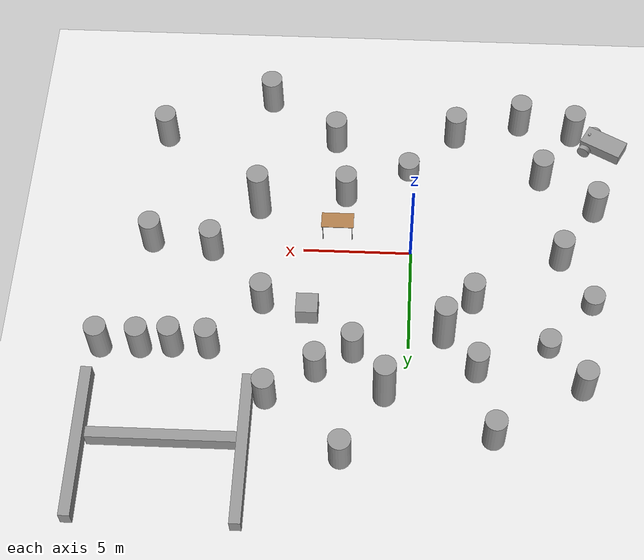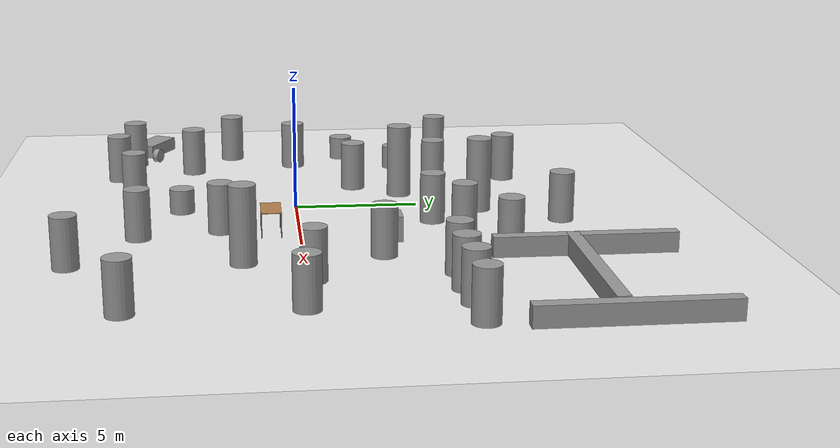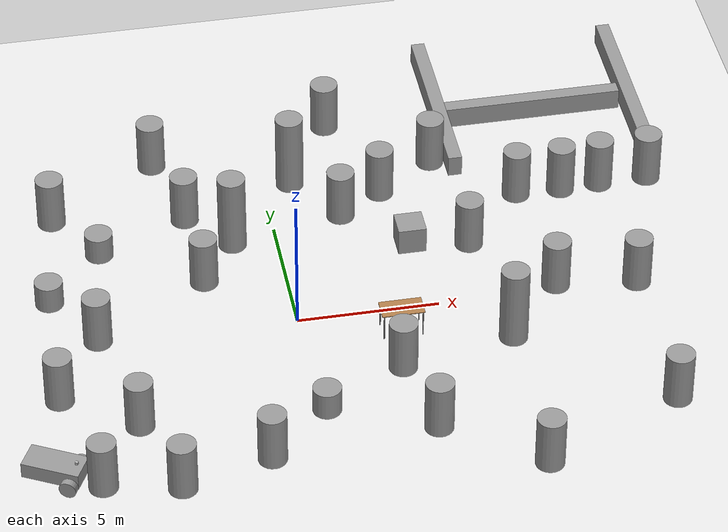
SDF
<sdf version="1.6">
 <world name="default">
  <scene><ambient>0.4 0.4 0.4 1</ambient><background>0.25 0.25 0.25 1</background><shadows>0</shadows></scene>
  <light name="sun" type="directional">
   <pose>0 0 10 0 -0 0</pose>
   <diffuse>0.7 0.7 0.7 0.5</diffuse>
   <specular>1 1 1 0.5</specular>
   <attenuation>
    <range>100</range>
    <constant>0.9</constant>
    <linear>0.01</linear>
    <quadratic>0.001</quadratic>
   </attenuation>
   <direction>0 0 -1</direction>
  </light>
  <model name="ground_plane">
   <static>1</static>
   <link name="link">
    <collision name="collision">
     <geometry><plane><normal>0 0 1</normal><size>100 100</size></plane></geometry>
     <surface><friction><ode><mu>100</mu><mu2>50</mu2></ode></friction></surface>
    </collision>
    <visual name="visual">
     <geometry><plane><normal>0 0 1</normal><size>100 100</size></plane></geometry>
     <material>
      <script><uri>file://media/materials/scripts/gazebo.material</uri><name>Gazebo/White</name></script>
     </material>
    </visual>
   </link>
  </model>
  <physics name="default_physics" default="0" type="ode">
   <ode>
    <solver>
     <type>quick</type>
     <iters>10</iters>
     <sor>1.3</sor>
     <use_dynamic_moi_rescaling>0</use_dynamic_moi_rescaling>
    </solver>
    <constraints>
     <cfm>0</cfm>
     <erp>0.2</erp>
     <contact_max_correcting_vel>100</contact_max_correcting_vel>
     <contact_surface_layer>0.001</contact_surface_layer>
    </constraints>
   </ode>
   <max_step_size>0.004</max_step_size>
   <real_time_factor>1</real_time_factor>
   <real_time_update_rate>250</real_time_update_rate>
  </physics>
  <gravity>0 0 -9.8066</gravity>
  <magnetic_field>6e-06 2.3e-05 -4.2e-05</magnetic_field>
  <atmosphere type="adiabatic"/>
  <scene><ambient>0.4 0.4 0.4 1</ambient><background>0.7 0.7 0.7 1</background><shadows>1</shadows></scene>
  <spherical_coordinates>
   <surface_model>EARTH_WGS84</surface_model>
   <latitude_deg>0</latitude_deg>
   <longitude_deg>0</longitude_deg>
   <elevation>0</elevation>
   <heading_deg>0</heading_deg>
  </spherical_coordinates>
  <model name="unit_cylinder_5_clone_1">
   <link name="link">
    <inertial>
     <mass>1</mass>
     <inertia><ixx>0.145833</ixx><ixy>0</ixy><ixz>0</ixz><iyy>0.145833</iyy><iyz>0</iyz><izz>0.125</izz></inertia>
    </inertial>
    <visual name="visual">
     <geometry><cylinder><radius>0.5</radius><length>2</length></cylinder></geometry>
     <material>
      <script><name>Gazebo/Grey</name><uri>file://media/materials/scripts/gazebo.material</uri></script>
      <ambient>0.3 0.3 0.3 1</ambient>
      <diffuse>0.7 0.7 0.7 1</diffuse>
      <specular>0.01 0.01 0.01 1</specular>
      <emissive>0 0 0 1</emissive>
      <shader type="vertex"><normal_map>__default__</normal_map></shader>
     </material>
    </visual>
    <collision name="collision">
     <geometry><cylinder><radius>0.5</radius><length>2</length></cylinder></geometry>
     <surface>
      <friction>
       <ode><mu>1</mu><mu2>1</mu2><fdir1>0 0 0</fdir1><slip1>0</slip1><slip2>0</slip2></ode>
       <torsional>
        <coefficient>1</coefficient>
        <patch_radius>0</patch_radius>
        <surface_radius>0</surface_radius>
        <use_patch_radius>1</use_patch_radius>
        <ode><slip>0</slip></ode>
       </torsional>
      </friction>
      <bounce><restitution_coefficient>0</restitution_coefficient><threshold>1e+06</threshold></bounce>
      <contact>
       <collide_without_contact>0</collide_without_contact>
       <collide_without_contact_bitmask>1</collide_without_contact_bitmask>
       <collide_bitmask>1</collide_bitmask>
       <ode>
        <soft_cfm>0</soft_cfm>
        <soft_erp>0.2</soft_erp>
        <kp>1e+13</kp>
        <kd>1</kd>
        <max_vel>0.01</max_vel>
        <min_depth>0</min_depth>
       </ode>
       <bullet>
        <split_impulse>1</split_impulse>
        <split_impulse_penetration_threshold>-0.01</split_impulse_penetration_threshold>
        <soft_cfm>0</soft_cfm>
        <soft_erp>0.2</soft_erp>
        <kp>1e+13</kp>
        <kd>1</kd>
       </bullet>
      </contact>
     </surface>
    </collision>
   </link>
   <static>0</static>
   <pose>-2.86936 2.60719 0.999884 2.2e-05 -1e-06 -0.002098</pose>
  </model>
  <model name="unit_cylinder_5_clone_4">
   <link name="link">
    <inertial>
     <mass>1</mass>
     <inertia><ixx>0.145833</ixx><ixy>0</ixy><ixz>0</ixz><iyy>0.145833</iyy><iyz>0</iyz><izz>0.125</izz></inertia>
    </inertial>
    <visual name="visual">
     <geometry><cylinder><radius>0.5</radius><length>2</length></cylinder></geometry>
     <material>
      <script><name>Gazebo/Grey</name><uri>file://media/materials/scripts/gazebo.material</uri></script>
      <ambient>0.3 0.3 0.3 1</ambient>
      <diffuse>0.7 0.7 0.7 1</diffuse>
      <specular>0.01 0.01 0.01 1</specular>
      <emissive>0 0 0 1</emissive>
      <shader type="vertex"><normal_map>__default__</normal_map></shader>
     </material>
    </visual>
    <collision name="collision">
     <geometry><cylinder><radius>0.5</radius><length>2</length></cylinder></geometry>
     <surface>
      <friction>
       <ode><mu>1</mu><mu2>1</mu2><fdir1>0 0 0</fdir1><slip1>0</slip1><slip2>0</slip2></ode>
       <torsional>
        <coefficient>1</coefficient>
        <patch_radius>0</patch_radius>
        <surface_radius>0</surface_radius>
        <use_patch_radius>1</use_patch_radius>
        <ode><slip>0</slip></ode>
       </torsional>
      </friction>
      <bounce><restitution_coefficient>0</restitution_coefficient><threshold>1e+06</threshold></bounce>
      <contact>
       <collide_without_contact>0</collide_without_contact>
       <collide_without_contact_bitmask>1</collide_without_contact_bitmask>
       <collide_bitmask>1</collide_bitmask>
       <ode>
        <soft_cfm>0</soft_cfm>
        <soft_erp>0.2</soft_erp>
        <kp>1e+13</kp>
        <kd>1</kd>
        <max_vel>0.01</max_vel>
        <min_depth>0</min_depth>
       </ode>
       <bullet>
        <split_impulse>1</split_impulse>
        <split_impulse_penetration_threshold>-0.01</split_impulse_penetration_threshold>
        <soft_cfm>0</soft_cfm>
        <soft_erp>0.2</soft_erp>
        <kp>1e+13</kp>
        <kd>1</kd>
       </bullet>
      </contact>
     </surface>
    </collision>
   </link>
   <static>0</static>
   <pose>-6.93374 0.169609 0.999884 2.2e-05 -1e-06 -0.003242</pose>
  </model>
  <model name="unit_cylinder_5_clone_5">
   <link name="link">
    <inertial>
     <mass>1</mass>
     <inertia><ixx>0.145833</ixx><ixy>0</ixy><ixz>0</ixz><iyy>0.145833</iyy><iyz>0</iyz><izz>0.125</izz></inertia>
    </inertial>
    <visual name="visual">
     <geometry><cylinder><radius>0.5</radius><length>2</length></cylinder></geometry>
     <material>
      <script><name>Gazebo/Grey</name><uri>file://media/materials/scripts/gazebo.material</uri></script>
      <ambient>0.3 0.3 0.3 1</ambient>
      <diffuse>0.7 0.7 0.7 1</diffuse>
      <specular>0.01 0.01 0.01 1</specular>
      <emissive>0 0 0 1</emissive>
      <shader type="vertex"><normal_map>__default__</normal_map></shader>
     </material>
    </visual>
    <collision name="collision">
     <geometry><cylinder><radius>0.5</radius><length>2</length></cylinder></geometry>
     <surface>
      <friction>
       <ode><mu>1</mu><mu2>1</mu2><fdir1>0 0 0</fdir1><slip1>0</slip1><slip2>0</slip2></ode>
       <torsional>
        <coefficient>1</coefficient>
        <patch_radius>0</patch_radius>
        <surface_radius>0</surface_radius>
        <use_patch_radius>1</use_patch_radius>
        <ode><slip>0</slip></ode>
       </torsional>
      </friction>
      <bounce><restitution_coefficient>0</restitution_coefficient><threshold>1e+06</threshold></bounce>
      <contact>
       <collide_without_contact>0</collide_without_contact>
       <collide_without_contact_bitmask>1</collide_without_contact_bitmask>
       <collide_bitmask>1</collide_bitmask>
       <ode>
        <soft_cfm>0</soft_cfm>
        <soft_erp>0.2</soft_erp>
        <kp>1e+13</kp>
        <kd>1</kd>
        <max_vel>0.01</max_vel>
        <min_depth>0</min_depth>
       </ode>
       <bullet>
        <split_impulse>1</split_impulse>
        <split_impulse_penetration_threshold>-0.01</split_impulse_penetration_threshold>
        <soft_cfm>0</soft_cfm>
        <soft_erp>0.2</soft_erp>
        <kp>1e+13</kp>
        <kd>1</kd>
       </bullet>
      </contact>
     </surface>
    </collision>
   </link>
   <static>0</static>
   <pose>-8.58869 -2.60634 0.999884 2.2e-05 -1e-06 -0.00565</pose>
  </model>
  <model name="unit_cylinder_5_clone_6">
   <link name="link">
    <inertial>
     <mass>1</mass>
     <inertia><ixx>0.145833</ixx><ixy>0</ixy><ixz>0</ixz><iyy>0.145833</iyy><iyz>0</iyz><izz>0.125</izz></inertia>
    </inertial>
    <visual name="visual">
     <geometry><cylinder><radius>0.5</radius><length>2</length></cylinder></geometry>
     <material>
      <script><name>Gazebo/Grey</name><uri>file://media/materials/scripts/gazebo.material</uri></script>
      <ambient>0.3 0.3 0.3 1</ambient>
      <diffuse>0.7 0.7 0.7 1</diffuse>
      <specular>0.01 0.01 0.01 1</specular>
      <emissive>0 0 0 1</emissive>
      <shader type="vertex"><normal_map>__default__</normal_map></shader>
     </material>
    </visual>
    <collision name="collision">
     <geometry><cylinder><radius>0.5</radius><length>2</length></cylinder></geometry>
     <surface>
      <friction>
       <ode><mu>1</mu><mu2>1</mu2><fdir1>0 0 0</fdir1><slip1>0</slip1><slip2>0</slip2></ode>
       <torsional>
        <coefficient>1</coefficient>
        <patch_radius>0</patch_radius>
        <surface_radius>0</surface_radius>
        <use_patch_radius>1</use_patch_radius>
        <ode><slip>0</slip></ode>
       </torsional>
      </friction>
      <bounce><restitution_coefficient>0</restitution_coefficient><threshold>1e+06</threshold></bounce>
      <contact>
       <collide_without_contact>0</collide_without_contact>
       <collide_without_contact_bitmask>1</collide_without_contact_bitmask>
       <collide_bitmask>1</collide_bitmask>
       <ode>
        <soft_cfm>0</soft_cfm>
        <soft_erp>0.2</soft_erp>
        <kp>1e+13</kp>
        <kd>1</kd>
        <max_vel>0.01</max_vel>
        <min_depth>0</min_depth>
       </ode>
       <bullet>
        <split_impulse>1</split_impulse>
        <split_impulse_penetration_threshold>-0.01</split_impulse_penetration_threshold>
        <soft_cfm>0</soft_cfm>
        <soft_erp>0.2</soft_erp>
        <kp>1e+13</kp>
        <kd>1</kd>
       </bullet>
      </contact>
     </surface>
    </collision>
   </link>
   <static>0</static>
   <pose>6.68619 2.97579 0.999884 2.2e-05 -1e-06 -0.00016</pose>
  </model>
  <model name="unit_box_0">
   <pose>4.62954 3.37214 0.499944 2e-06 -0.000108 -0.001417</pose>
   <link name="link">
    <inertial>
     <mass>1</mass>
     <inertia>
      <ixx>0.166667</ixx>
      <ixy>0</ixy>
      <ixz>0</ixz>
      <iyy>0.166667</iyy>
      <iyz>0</iyz>
      <izz>0.166667</izz>
     </inertia>
    </inertial>
    <collision name="collision"><geometry><box><size>1 1 1</size></box></geometry></collision>
    <visual name="visual">
     <geometry><box><size>1 1 1</size></box></geometry>
     <material>
      <script><name>Gazebo/Grey</name><uri>file://media/materials/scripts/gazebo.material</uri></script>
     </material>
    </visual>
   </link>
  </model>
  <model name="unit_cylinder_1">
   <pose>0.21006 -4.63987 0.499883 4e-06 -1e-06 -0.000351</pose>
   <link name="link">
    <inertial>
     <mass>1</mass>
     <inertia><ixx>0.145833</ixx><ixy>0</ixy><ixz>0</ixz><iyy>0.145833</iyy><iyz>0</iyz><izz>0.125</izz></inertia>
    </inertial>
    <collision name="collision">
     <geometry><cylinder><radius>0.5</radius><length>1</length></cylinder></geometry>
    </collision>
    <visual name="visual">
     <geometry><cylinder><radius>0.5</radius><length>1</length></cylinder></geometry>
     <material>
      <script><name>Gazebo/Grey</name><uri>file://media/materials/scripts/gazebo.material</uri></script>
     </material>
    </visual>
   </link>
  </model>
  <model name="unit_cylinder_1_clone_0">
   <pose>-6.29641 4.76433 0.499883 4e-06 -1e-06 -0.000309</pose>
   <link name="link">
    <inertial>
     <mass>1</mass>
     <inertia><ixx>0.145833</ixx><ixy>0</ixy><ixz>0</ixz><iyy>0.145833</iyy><iyz>0</iyz><izz>0.125</izz></inertia>
    </inertial>
    <collision name="collision">
     <geometry><cylinder><radius>0.5</radius><length>1</length></cylinder></geometry>
    </collision>
    <visual name="visual">
     <geometry><cylinder><radius>0.5</radius><length>1</length></cylinder></geometry>
     <material>
      <script><name>Gazebo/Grey</name><uri>file://media/materials/scripts/gazebo.material</uri></script>
     </material>
    </visual>
   </link>
  </model>
  <model name="unit_cylinder_1_clone_1">
   <pose>-8.3358 2.47751 0.499883 4e-06 -1e-06 0.00122</pose>
   <link name="link">
    <inertial>
     <mass>1</mass>
     <inertia><ixx>0.145833</ixx><ixy>0</ixy><ixz>0</ixz><iyy>0.145833</iyy><iyz>0</iyz><izz>0.125</izz></inertia>
    </inertial>
    <collision name="collision">
     <geometry><cylinder><radius>0.5</radius><length>1</length></cylinder></geometry>
    </collision>
    <visual name="visual">
     <geometry><cylinder><radius>0.5</radius><length>1</length></cylinder></geometry>
     <material>
      <script><name>Gazebo/Grey</name><uri>file://media/materials/scripts/gazebo.material</uri></script>
     </material>
    </visual>
   </link>
  </model>
  <model name="unit_cylinder_0_0">
   <link name="link">
    <inertial>
     <mass>1</mass>
     <inertia><ixx>0.145833</ixx><ixy>0</ixy><ixz>0</ixz><iyy>0.145833</iyy><iyz>0</iyz><izz>0.125</izz></inertia>
    </inertial>
    <visual name="visual">
     <geometry><cylinder><radius>0.5</radius><length>3</length></cylinder></geometry>
     <material>
      <script><name>Gazebo/Grey</name><uri>file://media/materials/scripts/gazebo.material</uri></script>
      <ambient>0.3 0.3 0.3 1</ambient>
      <diffuse>0.7 0.7 0.7 1</diffuse>
      <specular>0.01 0.01 0.01 1</specular>
      <emissive>0 0 0 1</emissive>
      <shader type="vertex"><normal_map>__default__</normal_map></shader>
     </material>
    </visual>
    <collision name="collision">
     <geometry><cylinder><radius>0.5</radius><length>3</length></cylinder></geometry>
     <surface>
      <friction>
       <ode><mu>1</mu><mu2>1</mu2><fdir1>0 0 0</fdir1><slip1>0</slip1><slip2>0</slip2></ode>
       <torsional>
        <coefficient>1</coefficient>
        <patch_radius>0</patch_radius>
        <surface_radius>0</surface_radius>
        <use_patch_radius>1</use_patch_radius>
        <ode><slip>0</slip></ode>
       </torsional>
      </friction>
      <bounce><restitution_coefficient>0</restitution_coefficient><threshold>1e+06</threshold></bounce>
      <contact>
       <collide_without_contact>0</collide_without_contact>
       <collide_without_contact_bitmask>1</collide_without_contact_bitmask>
       <collide_bitmask>1</collide_bitmask>
       <ode>
        <soft_cfm>0</soft_cfm>
        <soft_erp>0.2</soft_erp>
        <kp>1e+13</kp>
        <kd>1</kd>
        <max_vel>0.01</max_vel>
        <min_depth>0</min_depth>
       </ode>
       <bullet>
        <split_impulse>1</split_impulse>
        <split_impulse_penetration_threshold>-0.01</split_impulse_penetration_threshold>
        <soft_cfm>0</soft_cfm>
        <soft_erp>0.2</soft_erp>
        <kp>1e+13</kp>
        <kd>1</kd>
       </bullet>
      </contact>
     </surface>
    </collision>
   </link>
   <static>0</static>
   <pose>7.16655 -2.19561 1.49988 4.7e-05 -4e-06 -0.007363</pose>
  </model>
  <model name="unit_cylinder_5_clone_1_clone">
   <link name="link">
    <inertial>
     <mass>1</mass>
     <inertia><ixx>0.145833</ixx><ixy>0</ixy><ixz>0</ixz><iyy>0.145833</iyy><iyz>0</iyz><izz>0.125</izz></inertia>
    </inertial>
    <visual name="visual">
     <geometry><cylinder><radius>0.5</radius><length>2</length></cylinder></geometry>
     <material>
      <script><name>Gazebo/Grey</name><uri>file://media/materials/scripts/gazebo.material</uri></script>
      <ambient>0.3 0.3 0.3 1</ambient>
      <diffuse>0.7 0.7 0.7 1</diffuse>
      <specular>0.01 0.01 0.01 1</specular>
      <emissive>0 0 0 1</emissive>
      <shader type="vertex"><normal_map>__default__</normal_map></shader>
     </material>
    </visual>
    <collision name="collision">
     <geometry><cylinder><radius>0.5</radius><length>2</length></cylinder></geometry>
     <surface>
      <friction>
       <ode><mu>1</mu><mu2>1</mu2><fdir1>0 0 0</fdir1><slip1>0</slip1><slip2>0</slip2></ode>
       <torsional>
        <coefficient>1</coefficient>
        <patch_radius>0</patch_radius>
        <surface_radius>0</surface_radius>
        <use_patch_radius>1</use_patch_radius>
        <ode><slip>0</slip></ode>
       </torsional>
      </friction>
      <bounce><restitution_coefficient>0</restitution_coefficient><threshold>1e+06</threshold></bounce>
      <contact>
       <collide_without_contact>0</collide_without_contact>
       <collide_without_contact_bitmask>1</collide_without_contact_bitmask>
       <collide_bitmask>1</collide_bitmask>
       <ode>
        <soft_cfm>0</soft_cfm>
        <soft_erp>0.2</soft_erp>
        <kp>1e+13</kp>
        <kd>1</kd>
        <max_vel>0.01</max_vel>
        <min_depth>0</min_depth>
       </ode>
       <bullet>
        <split_impulse>1</split_impulse>
        <split_impulse_penetration_threshold>-0.01</split_impulse_penetration_threshold>
        <soft_cfm>0</soft_cfm>
        <soft_erp>0.2</soft_erp>
        <kp>1e+13</kp>
        <kd>1</kd>
       </bullet>
      </contact>
     </surface>
    </collision>
   </link>
   <static>0</static>
   <pose>2.48657 5.34635 0.999884 2.2e-05 -1e-06 -0.002572</pose>
  </model>
  <model name="unit_cylinder_5_clone_1_clone_0">
   <link name="link">
    <inertial>
     <mass>1</mass>
     <inertia><ixx>0.145833</ixx><ixy>0</ixy><ixz>0</ixz><iyy>0.145833</iyy><iyz>0</iyz><izz>0.125</izz></inertia>
    </inertial>
    <visual name="visual">
     <geometry><cylinder><radius>0.5</radius><length>2</length></cylinder></geometry>
     <material>
      <script><name>Gazebo/Grey</name><uri>file://media/materials/scripts/gazebo.material</uri></script>
      <ambient>0.3 0.3 0.3 1</ambient>
      <diffuse>0.7 0.7 0.7 1</diffuse>
      <specular>0.01 0.01 0.01 1</specular>
      <emissive>0 0 0 1</emissive>
      <shader type="vertex"><normal_map>__default__</normal_map></shader>
     </material>
    </visual>
    <collision name="collision">
     <geometry><cylinder><radius>0.5</radius><length>2</length></cylinder></geometry>
     <surface>
      <friction>
       <ode><mu>1</mu><mu2>1</mu2><fdir1>0 0 0</fdir1><slip1>0</slip1><slip2>0</slip2></ode>
       <torsional>
        <coefficient>1</coefficient>
        <patch_radius>0</patch_radius>
        <surface_radius>0</surface_radius>
        <use_patch_radius>1</use_patch_radius>
        <ode><slip>0</slip></ode>
       </torsional>
      </friction>
      <bounce><restitution_coefficient>0</restitution_coefficient><threshold>1e+06</threshold></bounce>
      <contact>
       <collide_without_contact>0</collide_without_contact>
       <collide_without_contact_bitmask>1</collide_without_contact_bitmask>
       <collide_bitmask>1</collide_bitmask>
       <ode>
        <soft_cfm>0</soft_cfm>
        <soft_erp>0.2</soft_erp>
        <kp>1e+13</kp>
        <kd>1</kd>
        <max_vel>0.01</max_vel>
        <min_depth>0</min_depth>
       </ode>
       <bullet>
        <split_impulse>1</split_impulse>
        <split_impulse_penetration_threshold>-0.01</split_impulse_penetration_threshold>
        <soft_cfm>0</soft_cfm>
        <soft_erp>0.2</soft_erp>
        <kp>1e+13</kp>
        <kd>1</kd>
       </bullet>
      </contact>
     </surface>
    </collision>
   </link>
   <static>0</static>
   <pose>-3.04049 6.13013 0.999884 2.2e-05 -1e-06 -0.001543</pose>
  </model>
  <model name="unit_cylinder_0_0_clone_clone">
   <link name="link">
    <inertial>
     <mass>1</mass>
     <inertia><ixx>0.145833</ixx><ixy>0</ixy><ixz>0</ixz><iyy>0.145833</iyy><iyz>0</iyz><izz>0.125</izz></inertia>
    </inertial>
    <visual name="visual">
     <geometry><cylinder><radius>0.5</radius><length>3</length></cylinder></geometry>
     <material>
      <script><name>Gazebo/Grey</name><uri>file://media/materials/scripts/gazebo.material</uri></script>
      <ambient>0.3 0.3 0.3 1</ambient>
      <diffuse>0.7 0.7 0.7 1</diffuse>
      <specular>0.01 0.01 0.01 1</specular>
      <emissive>0 0 0 1</emissive>
      <shader type="vertex"><normal_map>__default__</normal_map></shader>
     </material>
    </visual>
    <collision name="collision">
     <geometry><cylinder><radius>0.5</radius><length>3</length></cylinder></geometry>
     <surface>
      <friction>
       <ode><mu>1</mu><mu2>1</mu2><fdir1>0 0 0</fdir1><slip1>0</slip1><slip2>0</slip2></ode>
       <torsional>
        <coefficient>1</coefficient>
        <patch_radius>0</patch_radius>
        <surface_radius>0</surface_radius>
        <use_patch_radius>1</use_patch_radius>
        <ode><slip>0</slip></ode>
       </torsional>
      </friction>
      <bounce><restitution_coefficient>0</restitution_coefficient><threshold>1e+06</threshold></bounce>
      <contact>
       <collide_without_contact>0</collide_without_contact>
       <collide_without_contact_bitmask>1</collide_without_contact_bitmask>
       <collide_bitmask>1</collide_bitmask>
       <ode>
        <soft_cfm>0</soft_cfm>
        <soft_erp>0.2</soft_erp>
        <kp>1e+13</kp>
        <kd>1</kd>
        <max_vel>0.01</max_vel>
        <min_depth>0</min_depth>
       </ode>
       <bullet>
        <split_impulse>1</split_impulse>
        <split_impulse_penetration_threshold>-0.01</split_impulse_penetration_threshold>
        <soft_cfm>0</soft_cfm>
        <soft_erp>0.2</soft_erp>
        <kp>1e+13</kp>
        <kd>1</kd>
       </bullet>
      </contact>
     </surface>
    </collision>
   </link>
   <static>0</static>
   <pose>1.00258 7.45887 1.49988 4.7e-05 -3e-06 -0.011031</pose>
  </model>
  <model name="unit_cylinder_0_0_clone_clone_1">
   <link name="link">
    <inertial>
     <mass>1</mass>
     <inertia><ixx>0.145833</ixx><ixy>0</ixy><ixz>0</ixz><iyy>0.145833</iyy><iyz>0</iyz><izz>0.125</izz></inertia>
    </inertial>
    <visual name="visual">
     <geometry><cylinder><radius>0.5</radius><length>3</length></cylinder></geometry>
     <material>
      <script><name>Gazebo/Grey</name><uri>file://media/materials/scripts/gazebo.material</uri></script>
      <ambient>0.3 0.3 0.3 1</ambient>
      <diffuse>0.7 0.7 0.7 1</diffuse>
      <specular>0.01 0.01 0.01 1</specular>
      <emissive>0 0 0 1</emissive>
      <shader type="vertex"><normal_map>__default__</normal_map></shader>
     </material>
    </visual>
    <collision name="collision">
     <geometry><cylinder><radius>0.5</radius><length>3</length></cylinder></geometry>
     <surface>
      <friction>
       <ode><mu>1</mu><mu2>1</mu2><fdir1>0 0 0</fdir1><slip1>0</slip1><slip2>0</slip2></ode>
       <torsional>
        <coefficient>1</coefficient>
        <patch_radius>0</patch_radius>
        <surface_radius>0</surface_radius>
        <use_patch_radius>1</use_patch_radius>
        <ode><slip>0</slip></ode>
       </torsional>
      </friction>
      <bounce><restitution_coefficient>0</restitution_coefficient><threshold>1e+06</threshold></bounce>
      <contact>
       <collide_without_contact>0</collide_without_contact>
       <collide_without_contact_bitmask>1</collide_without_contact_bitmask>
       <collide_bitmask>1</collide_bitmask>
       <ode>
        <soft_cfm>0</soft_cfm>
        <soft_erp>0.2</soft_erp>
        <kp>1e+13</kp>
        <kd>1</kd>
        <max_vel>0.01</max_vel>
        <min_depth>0</min_depth>
       </ode>
       <bullet>
        <split_impulse>1</split_impulse>
        <split_impulse_penetration_threshold>-0.01</split_impulse_penetration_threshold>
        <soft_cfm>0</soft_cfm>
        <soft_erp>0.2</soft_erp>
        <kp>1e+13</kp>
        <kd>1</kd>
       </bullet>
      </contact>
     </surface>
    </collision>
   </link>
   <static>0</static>
   <pose>-1.56827 4.46661 1.49988 4.7e-05 4e-06 0.007604</pose>
  </model>
  <model name="unit_cylinder_5_clone_0_clone">
   <link name="link">
    <inertial>
     <mass>1</mass>
     <inertia><ixx>0.145833</ixx><ixy>0</ixy><ixz>0</ixz><iyy>0.145833</iyy><iyz>0</iyz><izz>0.125</izz></inertia>
    </inertial>
    <visual name="visual">
     <geometry><cylinder><radius>0.5</radius><length>2</length></cylinder></geometry>
     <material>
      <script><name>Gazebo/Grey</name><uri>file://media/materials/scripts/gazebo.material</uri></script>
      <ambient>0.3 0.3 0.3 1</ambient>
      <diffuse>0.7 0.7 0.7 1</diffuse>
      <specular>0.01 0.01 0.01 1</specular>
      <emissive>0 0 0 1</emissive>
      <shader type="vertex"><normal_map>__default__</normal_map></shader>
     </material>
    </visual>
    <collision name="collision">
     <geometry><cylinder><radius>0.5</radius><length>2</length></cylinder></geometry>
     <surface>
      <friction>
       <ode><mu>1</mu><mu2>1</mu2><fdir1>0 0 0</fdir1><slip1>0</slip1><slip2>0</slip2></ode>
       <torsional>
        <coefficient>1</coefficient>
        <patch_radius>0</patch_radius>
        <surface_radius>0</surface_radius>
        <use_patch_radius>1</use_patch_radius>
        <ode><slip>0</slip></ode>
       </torsional>
      </friction>
      <bounce><restitution_coefficient>0</restitution_coefficient><threshold>1e+06</threshold></bounce>
      <contact>
       <collide_without_contact>0</collide_without_contact>
       <collide_without_contact_bitmask>1</collide_without_contact_bitmask>
       <collide_bitmask>1</collide_bitmask>
       <ode>
        <soft_cfm>0</soft_cfm>
        <soft_erp>0.2</soft_erp>
        <kp>1e+13</kp>
        <kd>1</kd>
        <max_vel>0.01</max_vel>
        <min_depth>0</min_depth>
       </ode>
       <bullet>
        <split_impulse>1</split_impulse>
        <split_impulse_penetration_threshold>-0.01</split_impulse_penetration_threshold>
        <soft_cfm>0</soft_cfm>
        <soft_erp>0.2</soft_erp>
        <kp>1e+13</kp>
        <kd>1</kd>
       </bullet>
      </contact>
     </surface>
    </collision>
   </link>
   <static>0</static>
   <pose>3.1338 -3.03553 0.999884 2.2e-05 -2e-06 0.003362</pose>
  </model>
  <model name="unit_cylinder_5_clone_0_clone_1">
   <link name="link">
    <inertial>
     <mass>1</mass>
     <inertia><ixx>0.145833</ixx><ixy>0</ixy><ixz>0</ixz><iyy>0.145833</iyy><iyz>0</iyz><izz>0.125</izz></inertia>
    </inertial>
    <visual name="visual">
     <geometry><cylinder><radius>0.5</radius><length>2</length></cylinder></geometry>
     <material>
      <script><name>Gazebo/Grey</name><uri>file://media/materials/scripts/gazebo.material</uri></script>
      <ambient>0.3 0.3 0.3 1</ambient>
      <diffuse>0.7 0.7 0.7 1</diffuse>
      <specular>0.01 0.01 0.01 1</specular>
      <emissive>0 0 0 1</emissive>
      <shader type="vertex"><normal_map>__default__</normal_map></shader>
     </material>
    </visual>
    <collision name="collision">
     <geometry><cylinder><radius>0.5</radius><length>2</length></cylinder></geometry>
     <surface>
      <friction>
       <ode><mu>1</mu><mu2>1</mu2><fdir1>0 0 0</fdir1><slip1>0</slip1><slip2>0</slip2></ode>
       <torsional>
        <coefficient>1</coefficient>
        <patch_radius>0</patch_radius>
        <surface_radius>0</surface_radius>
        <use_patch_radius>1</use_patch_radius>
        <ode><slip>0</slip></ode>
       </torsional>
      </friction>
      <bounce><restitution_coefficient>0</restitution_coefficient><threshold>1e+06</threshold></bounce>
      <contact>
       <collide_without_contact>0</collide_without_contact>
       <collide_without_contact_bitmask>1</collide_without_contact_bitmask>
       <collide_bitmask>1</collide_bitmask>
       <ode>
        <soft_cfm>0</soft_cfm>
        <soft_erp>0.2</soft_erp>
        <kp>1e+13</kp>
        <kd>1</kd>
        <max_vel>0.01</max_vel>
        <min_depth>0</min_depth>
       </ode>
       <bullet>
        <split_impulse>1</split_impulse>
        <split_impulse_penetration_threshold>-0.01</split_impulse_penetration_threshold>
        <soft_cfm>0</soft_cfm>
        <soft_erp>0.2</soft_erp>
        <kp>1e+13</kp>
        <kd>1</kd>
       </bullet>
      </contact>
     </surface>
    </collision>
   </link>
   <static>0</static>
   <pose>-1.98793 -6.68678 0.999884 2.2e-05 -1e-06 0.001991</pose>
  </model>
  <model name="unit_cylinder_5_clone_0_clone_2">
   <link name="link">
    <inertial>
     <mass>1</mass>
     <inertia><ixx>0.145833</ixx><ixy>0</ixy><ixz>0</ixz><iyy>0.145833</iyy><iyz>0</iyz><izz>0.125</izz></inertia>
    </inertial>
    <visual name="visual">
     <geometry><cylinder><radius>0.5</radius><length>2</length></cylinder></geometry>
     <material>
      <script><name>Gazebo/Grey</name><uri>file://media/materials/scripts/gazebo.material</uri></script>
      <ambient>0.3 0.3 0.3 1</ambient>
      <diffuse>0.7 0.7 0.7 1</diffuse>
      <specular>0.01 0.01 0.01 1</specular>
      <emissive>0 0 0 1</emissive>
      <shader type="vertex"><normal_map>__default__</normal_map></shader>
     </material>
    </visual>
    <collision name="collision">
     <geometry><cylinder><radius>0.5</radius><length>2</length></cylinder></geometry>
     <surface>
      <friction>
       <ode><mu>1</mu><mu2>1</mu2><fdir1>0 0 0</fdir1><slip1>0</slip1><slip2>0</slip2></ode>
       <torsional>
        <coefficient>1</coefficient>
        <patch_radius>0</patch_radius>
        <surface_radius>0</surface_radius>
        <use_patch_radius>1</use_patch_radius>
        <ode><slip>0</slip></ode>
       </torsional>
      </friction>
      <bounce><restitution_coefficient>0</restitution_coefficient><threshold>1e+06</threshold></bounce>
      <contact>
       <collide_without_contact>0</collide_without_contact>
       <collide_without_contact_bitmask>1</collide_without_contact_bitmask>
       <collide_bitmask>1</collide_bitmask>
       <ode>
        <soft_cfm>0</soft_cfm>
        <soft_erp>0.2</soft_erp>
        <kp>1e+13</kp>
        <kd>1</kd>
        <max_vel>0.01</max_vel>
        <min_depth>0</min_depth>
       </ode>
       <bullet>
        <split_impulse>1</split_impulse>
        <split_impulse_penetration_threshold>-0.01</split_impulse_penetration_threshold>
        <soft_cfm>0</soft_cfm>
        <soft_erp>0.2</soft_erp>
        <kp>1e+13</kp>
        <kd>1</kd>
       </bullet>
      </contact>
     </surface>
    </collision>
   </link>
   <static>0</static>
   <pose>3.74075 -6.19025 0.999884 2.2e-05 -1e-06 0.00233</pose>
  </model>
  <model name="unit_cylinder_5_clone_0_clone_4">
   <link name="link">
    <inertial>
     <mass>1</mass>
     <inertia><ixx>0.145833</ixx><ixy>0</ixy><ixz>0</ixz><iyy>0.145833</iyy><iyz>0</iyz><izz>0.125</izz></inertia>
    </inertial>
    <visual name="visual">
     <geometry><cylinder><radius>0.5</radius><length>2</length></cylinder></geometry>
     <material>
      <script><name>Gazebo/Grey</name><uri>file://media/materials/scripts/gazebo.material</uri></script>
      <ambient>0.3 0.3 0.3 1</ambient>
      <diffuse>0.7 0.7 0.7 1</diffuse>
      <specular>0.01 0.01 0.01 1</specular>
      <emissive>0 0 0 1</emissive>
      <shader type="vertex"><normal_map>__default__</normal_map></shader>
     </material>
    </visual>
    <collision name="collision">
     <geometry><cylinder><radius>0.5</radius><length>2</length></cylinder></geometry>
     <surface>
      <friction>
       <ode><mu>1</mu><mu2>1</mu2><fdir1>0 0 0</fdir1><slip1>0</slip1><slip2>0</slip2></ode>
       <torsional>
        <coefficient>1</coefficient>
        <patch_radius>0</patch_radius>
        <surface_radius>0</surface_radius>
        <use_patch_radius>1</use_patch_radius>
        <ode><slip>0</slip></ode>
       </torsional>
      </friction>
      <bounce><restitution_coefficient>0</restitution_coefficient><threshold>1e+06</threshold></bounce>
      <contact>
       <collide_without_contact>0</collide_without_contact>
       <collide_without_contact_bitmask>1</collide_without_contact_bitmask>
       <collide_bitmask>1</collide_bitmask>
       <ode>
        <soft_cfm>0</soft_cfm>
        <soft_erp>0.2</soft_erp>
        <kp>1e+13</kp>
        <kd>1</kd>
        <max_vel>0.01</max_vel>
        <min_depth>0</min_depth>
       </ode>
       <bullet>
        <split_impulse>1</split_impulse>
        <split_impulse_penetration_threshold>-0.01</split_impulse_penetration_threshold>
        <soft_cfm>0</soft_cfm>
        <soft_erp>0.2</soft_erp>
        <kp>1e+13</kp>
        <kd>1</kd>
       </bullet>
      </contact>
     </surface>
    </collision>
   </link>
   <static>0</static>
   <pose>6.23609 7.78202 0.999884 2.2e-05 -1e-06 0.001596</pose>
  </model>
  <model name="unit_cylinder_5_clone_0_clone_5">
   <link name="link">
    <inertial>
     <mass>1</mass>
     <inertia><ixx>0.145833</ixx><ixy>0</ixy><ixz>0</ixz><iyy>0.145833</iyy><iyz>0</iyz><izz>0.125</izz></inertia>
    </inertial>
    <visual name="visual">
     <geometry><cylinder><radius>0.5</radius><length>2</length></cylinder></geometry>
     <material>
      <script><name>Gazebo/Grey</name><uri>file://media/materials/scripts/gazebo.material</uri></script>
      <ambient>0.3 0.3 0.3 1</ambient>
      <diffuse>0.7 0.7 0.7 1</diffuse>
      <specular>0.01 0.01 0.01 1</specular>
      <emissive>0 0 0 1</emissive>
      <shader type="vertex"><normal_map>__default__</normal_map></shader>
     </material>
    </visual>
    <collision name="collision">
     <geometry><cylinder><radius>0.5</radius><length>2</length></cylinder></geometry>
     <surface>
      <friction>
       <ode><mu>1</mu><mu2>1</mu2><fdir1>0 0 0</fdir1><slip1>0</slip1><slip2>0</slip2></ode>
       <torsional>
        <coefficient>1</coefficient>
        <patch_radius>0</patch_radius>
        <surface_radius>0</surface_radius>
        <use_patch_radius>1</use_patch_radius>
        <ode><slip>0</slip></ode>
       </torsional>
      </friction>
      <bounce><restitution_coefficient>0</restitution_coefficient><threshold>1e+06</threshold></bounce>
      <contact>
       <collide_without_contact>0</collide_without_contact>
       <collide_without_contact_bitmask>1</collide_without_contact_bitmask>
       <collide_bitmask>1</collide_bitmask>
       <ode>
        <soft_cfm>0</soft_cfm>
        <soft_erp>0.2</soft_erp>
        <kp>1e+13</kp>
        <kd>1</kd>
        <max_vel>0.01</max_vel>
        <min_depth>0</min_depth>
       </ode>
       <bullet>
        <split_impulse>1</split_impulse>
        <split_impulse_penetration_threshold>-0.01</split_impulse_penetration_threshold>
        <soft_cfm>0</soft_cfm>
        <soft_erp>0.2</soft_erp>
        <kp>1e+13</kp>
        <kd>1</kd>
       </bullet>
      </contact>
     </surface>
    </collision>
   </link>
   <static>0</static>
   <pose>4.1001 6.37047 0.999884 2.2e-05 -1e-06 0.001336</pose>
  </model>
  <model name="unit_cylinder_5_clone_0_clone_6">
   <link name="link">
    <inertial>
     <mass>1</mass>
     <inertia><ixx>0.145833</ixx><ixy>0</ixy><ixz>0</ixz><iyy>0.145833</iyy><iyz>0</iyz><izz>0.125</izz></inertia>
    </inertial>
    <visual name="visual">
     <geometry><cylinder><radius>0.5</radius><length>2</length></cylinder></geometry>
     <material>
      <script><name>Gazebo/Grey</name><uri>file://media/materials/scripts/gazebo.material</uri></script>
      <ambient>0.3 0.3 0.3 1</ambient>
      <diffuse>0.7 0.7 0.7 1</diffuse>
      <specular>0.01 0.01 0.01 1</specular>
      <emissive>0 0 0 1</emissive>
      <shader type="vertex"><normal_map>__default__</normal_map></shader>
     </material>
    </visual>
    <collision name="collision">
     <geometry><cylinder><radius>0.5</radius><length>2</length></cylinder></geometry>
     <surface>
      <friction>
       <ode><mu>1</mu><mu2>1</mu2><fdir1>0 0 0</fdir1><slip1>0</slip1><slip2>0</slip2></ode>
       <torsional>
        <coefficient>1</coefficient>
        <patch_radius>0</patch_radius>
        <surface_radius>0</surface_radius>
        <use_patch_radius>1</use_patch_radius>
        <ode><slip>0</slip></ode>
       </torsional>
      </friction>
      <bounce><restitution_coefficient>0</restitution_coefficient><threshold>1e+06</threshold></bounce>
      <contact>
       <collide_without_contact>0</collide_without_contact>
       <collide_without_contact_bitmask>1</collide_without_contact_bitmask>
       <collide_bitmask>1</collide_bitmask>
       <ode>
        <soft_cfm>0</soft_cfm>
        <soft_erp>0.2</soft_erp>
        <kp>1e+13</kp>
        <kd>1</kd>
        <max_vel>0.01</max_vel>
        <min_depth>0</min_depth>
       </ode>
       <bullet>
        <split_impulse>1</split_impulse>
        <split_impulse_penetration_threshold>-0.01</split_impulse_penetration_threshold>
        <soft_cfm>0</soft_cfm>
        <soft_erp>0.2</soft_erp>
        <kp>1e+13</kp>
        <kd>1</kd>
       </bullet>
      </contact>
     </surface>
    </collision>
   </link>
   <static>0</static>
   <pose>-7.74649 6.83596 0.999884 2.2e-05 -1e-06 0.001268</pose>
  </model>
  <model name="unit_cylinder_5_clone_0_clone_7">
   <link name="link">
    <inertial>
     <mass>1</mass>
     <inertia><ixx>0.145833</ixx><ixy>0</ixy><ixz>0</ixz><iyy>0.145833</iyy><iyz>0</iyz><izz>0.125</izz></inertia>
    </inertial>
    <visual name="visual">
     <geometry><cylinder><radius>0.5</radius><length>2</length></cylinder></geometry>
     <material>
      <script><name>Gazebo/Grey</name><uri>file://media/materials/scripts/gazebo.material</uri></script>
      <ambient>0.3 0.3 0.3 1</ambient>
      <diffuse>0.7 0.7 0.7 1</diffuse>
      <specular>0.01 0.01 0.01 1</specular>
      <emissive>0 0 0 1</emissive>
      <shader type="vertex"><normal_map>__default__</normal_map></shader>
     </material>
    </visual>
    <collision name="collision">
     <geometry><cylinder><radius>0.5</radius><length>2</length></cylinder></geometry>
     <surface>
      <friction>
       <ode><mu>1</mu><mu2>1</mu2><fdir1>0 0 0</fdir1><slip1>0</slip1><slip2>0</slip2></ode>
       <torsional>
        <coefficient>1</coefficient>
        <patch_radius>0</patch_radius>
        <surface_radius>0</surface_radius>
        <use_patch_radius>1</use_patch_radius>
        <ode><slip>0</slip></ode>
       </torsional>
      </friction>
      <bounce><restitution_coefficient>0</restitution_coefficient><threshold>1e+06</threshold></bounce>
      <contact>
       <collide_without_contact>0</collide_without_contact>
       <collide_without_contact_bitmask>1</collide_without_contact_bitmask>
       <collide_bitmask>1</collide_bitmask>
       <ode>
        <soft_cfm>0</soft_cfm>
        <soft_erp>0.2</soft_erp>
        <kp>1e+13</kp>
        <kd>1</kd>
        <max_vel>0.01</max_vel>
        <min_depth>0</min_depth>
       </ode>
       <bullet>
        <split_impulse>1</split_impulse>
        <split_impulse_penetration_threshold>-0.01</split_impulse_penetration_threshold>
        <soft_cfm>0</soft_cfm>
        <soft_erp>0.2</soft_erp>
        <kp>1e+13</kp>
        <kd>1</kd>
       </bullet>
      </contact>
     </surface>
    </collision>
   </link>
   <static>0</static>
   <pose>-6.09067 -4.32217 0.999884 2.2e-05 -1e-06 0.000743</pose>
  </model>
  <model name="unit_cylinder_5_clone_0_clone_8">
   <link name="link">
    <inertial>
     <mass>1</mass>
     <inertia><ixx>0.145833</ixx><ixy>0</ixy><ixz>0</ixz><iyy>0.145833</iyy><iyz>0</iyz><izz>0.125</izz></inertia>
    </inertial>
    <visual name="visual">
     <geometry><cylinder><radius>0.5</radius><length>2</length></cylinder></geometry>
     <material>
      <script><name>Gazebo/Grey</name><uri>file://media/materials/scripts/gazebo.material</uri></script>
      <ambient>0.3 0.3 0.3 1</ambient>
      <diffuse>0.7 0.7 0.7 1</diffuse>
      <specular>0.01 0.01 0.01 1</specular>
      <emissive>0 0 0 1</emissive>
      <shader type="vertex"><normal_map>__default__</normal_map></shader>
     </material>
    </visual>
    <collision name="collision">
     <geometry><cylinder><radius>0.5</radius><length>2</length></cylinder></geometry>
     <surface>
      <friction>
       <ode><mu>1</mu><mu2>1</mu2><fdir1>0 0 0</fdir1><slip1>0</slip1><slip2>0</slip2></ode>
       <torsional>
        <coefficient>1</coefficient>
        <patch_radius>0</patch_radius>
        <surface_radius>0</surface_radius>
        <use_patch_radius>1</use_patch_radius>
        <ode><slip>0</slip></ode>
       </torsional>
      </friction>
      <bounce><restitution_coefficient>0</restitution_coefficient><threshold>1e+06</threshold></bounce>
      <contact>
       <collide_without_contact>0</collide_without_contact>
       <collide_without_contact_bitmask>1</collide_without_contact_bitmask>
       <collide_bitmask>1</collide_bitmask>
       <ode>
        <soft_cfm>0</soft_cfm>
        <soft_erp>0.2</soft_erp>
        <kp>1e+13</kp>
        <kd>1</kd>
        <max_vel>0.01</max_vel>
        <min_depth>0</min_depth>
       </ode>
       <bullet>
        <split_impulse>1</split_impulse>
        <split_impulse_penetration_threshold>-0.01</split_impulse_penetration_threshold>
        <soft_cfm>0</soft_cfm>
        <soft_erp>0.2</soft_erp>
        <kp>1e+13</kp>
        <kd>1</kd>
       </bullet>
      </contact>
     </surface>
    </collision>
   </link>
   <static>0</static>
   <pose>-7.67513 -7.00944 0.999884 2.2e-05 -1e-06 5e-05</pose>
  </model>
  <model name="unit_cylinder_5_clone_0_clone_9">
   <link name="link">
    <inertial>
     <mass>1</mass>
     <inertia><ixx>0.145833</ixx><ixy>0</ixy><ixz>0</ixz><iyy>0.145833</iyy><iyz>0</iyz><izz>0.125</izz></inertia>
    </inertial>
    <visual name="visual">
     <geometry><cylinder><radius>0.5</radius><length>2</length></cylinder></geometry>
     <material>
      <script><name>Gazebo/Grey</name><uri>file://media/materials/scripts/gazebo.material</uri></script>
      <ambient>0.3 0.3 0.3 1</ambient>
      <diffuse>0.7 0.7 0.7 1</diffuse>
      <specular>0.01 0.01 0.01 1</specular>
      <emissive>0 0 0 1</emissive>
      <shader type="vertex"><normal_map>__default__</normal_map></shader>
     </material>
    </visual>
    <collision name="collision">
     <geometry><cylinder><radius>0.5</radius><length>2</length></cylinder></geometry>
     <surface>
      <friction>
       <ode><mu>1</mu><mu2>1</mu2><fdir1>0 0 0</fdir1><slip1>0</slip1><slip2>0</slip2></ode>
       <torsional>
        <coefficient>1</coefficient>
        <patch_radius>0</patch_radius>
        <surface_radius>0</surface_radius>
        <use_patch_radius>1</use_patch_radius>
        <ode><slip>0</slip></ode>
       </torsional>
      </friction>
      <bounce><restitution_coefficient>0</restitution_coefficient><threshold>1e+06</threshold></bounce>
      <contact>
       <collide_without_contact>0</collide_without_contact>
       <collide_without_contact_bitmask>1</collide_without_contact_bitmask>
       <collide_bitmask>1</collide_bitmask>
       <ode>
        <soft_cfm>0</soft_cfm>
        <soft_erp>0.2</soft_erp>
        <kp>1e+13</kp>
        <kd>1</kd>
        <max_vel>0.01</max_vel>
        <min_depth>0</min_depth>
       </ode>
       <bullet>
        <split_impulse>1</split_impulse>
        <split_impulse_penetration_threshold>-0.01</split_impulse_penetration_threshold>
        <soft_cfm>0</soft_cfm>
        <soft_erp>0.2</soft_erp>
        <kp>1e+13</kp>
        <kd>1</kd>
       </bullet>
      </contact>
     </surface>
    </collision>
   </link>
   <static>0</static>
   <pose>-5.11629 -7.54679 0.999884 2.2e-05 -1e-06 0.000502</pose>
  </model>
  <model name="unit_cylinder_5_clone_7_clone">
   <link name="link">
    <inertial>
     <mass>1</mass>
     <inertia><ixx>0.145833</ixx><ixy>0</ixy><ixz>0</ixz><iyy>0.145833</iyy><iyz>0</iyz><izz>0.125</izz></inertia>
    </inertial>
    <visual name="visual">
     <geometry><cylinder><radius>0.5</radius><length>2</length></cylinder></geometry>
     <material>
      <script><name>Gazebo/Grey</name><uri>file://media/materials/scripts/gazebo.material</uri></script>
      <ambient>0.3 0.3 0.3 1</ambient>
      <diffuse>0.7 0.7 0.7 1</diffuse>
      <specular>0.01 0.01 0.01 1</specular>
      <emissive>0 0 0 1</emissive>
      <shader type="vertex"><normal_map>__default__</normal_map></shader>
     </material>
    </visual>
    <collision name="collision">
     <geometry><cylinder><radius>0.5</radius><length>2</length></cylinder></geometry>
     <surface>
      <friction>
       <ode><mu>1</mu><mu2>1</mu2><fdir1>0 0 0</fdir1><slip1>0</slip1><slip2>0</slip2></ode>
       <torsional>
        <coefficient>1</coefficient>
        <patch_radius>0</patch_radius>
        <surface_radius>0</surface_radius>
        <use_patch_radius>1</use_patch_radius>
        <ode><slip>0</slip></ode>
       </torsional>
      </friction>
      <bounce><restitution_coefficient>0</restitution_coefficient><threshold>1e+06</threshold></bounce>
      <contact>
       <collide_without_contact>0</collide_without_contact>
       <collide_without_contact_bitmask>1</collide_without_contact_bitmask>
       <collide_bitmask>1</collide_bitmask>
       <ode>
        <soft_cfm>0</soft_cfm>
        <soft_erp>0.2</soft_erp>
        <kp>1e+13</kp>
        <kd>1</kd>
        <max_vel>0.01</max_vel>
        <min_depth>0</min_depth>
       </ode>
       <bullet>
        <split_impulse>1</split_impulse>
        <split_impulse_penetration_threshold>-0.01</split_impulse_penetration_threshold>
        <soft_cfm>0</soft_cfm>
        <soft_erp>0.2</soft_erp>
        <kp>1e+13</kp>
        <kd>1</kd>
       </bullet>
      </contact>
     </surface>
    </collision>
   </link>
   <static>0</static>
   <pose>8.9336 5.39085 0.999884 2.2e-05 -1e-06 0.002003</pose>
  </model>
  <model name="unit_cylinder_5_clone_7_clone_0">
   <link name="link">
    <inertial>
     <mass>1</mass>
     <inertia><ixx>0.145833</ixx><ixy>0</ixy><ixz>0</ixz><iyy>0.145833</iyy><iyz>0</iyz><izz>0.125</izz></inertia>
    </inertial>
    <visual name="visual">
     <geometry><cylinder><radius>0.5</radius><length>2</length></cylinder></geometry>
     <material>
      <script><name>Gazebo/Grey</name><uri>file://media/materials/scripts/gazebo.material</uri></script>
      <ambient>0.3 0.3 0.3 1</ambient>
      <diffuse>0.7 0.7 0.7 1</diffuse>
      <specular>0.01 0.01 0.01 1</specular>
      <emissive>0 0 0 1</emissive>
      <shader type="vertex"><normal_map>__default__</normal_map></shader>
     </material>
    </visual>
    <collision name="collision">
     <geometry><cylinder><radius>0.5</radius><length>2</length></cylinder></geometry>
     <surface>
      <friction>
       <ode><mu>1</mu><mu2>1</mu2><fdir1>0 0 0</fdir1><slip1>0</slip1><slip2>0</slip2></ode>
       <torsional>
        <coefficient>1</coefficient>
        <patch_radius>0</patch_radius>
        <surface_radius>0</surface_radius>
        <use_patch_radius>1</use_patch_radius>
        <ode><slip>0</slip></ode>
       </torsional>
      </friction>
      <bounce><restitution_coefficient>0</restitution_coefficient><threshold>1e+06</threshold></bounce>
      <contact>
       <collide_without_contact>0</collide_without_contact>
       <collide_without_contact_bitmask>1</collide_without_contact_bitmask>
       <collide_bitmask>1</collide_bitmask>
       <ode>
        <soft_cfm>0</soft_cfm>
        <soft_erp>0.2</soft_erp>
        <kp>1e+13</kp>
        <kd>1</kd>
        <max_vel>0.01</max_vel>
        <min_depth>0</min_depth>
       </ode>
       <bullet>
        <split_impulse>1</split_impulse>
        <split_impulse_penetration_threshold>-0.01</split_impulse_penetration_threshold>
        <soft_cfm>0</soft_cfm>
        <soft_erp>0.2</soft_erp>
        <kp>1e+13</kp>
        <kd>1</kd>
       </bullet>
      </contact>
     </surface>
    </collision>
   </link>
   <static>0</static>
   <pose>10.566 5.36918 0.999884 2.2e-05 -1e-06 0.001966</pose>
  </model>
  <model name="unit_cylinder_5_clone_7_clone_1">
   <link name="link">
    <inertial>
     <mass>1</mass>
     <inertia><ixx>0.145833</ixx><ixy>0</ixy><ixz>0</ixz><iyy>0.145833</iyy><iyz>0</iyz><izz>0.125</izz></inertia>
    </inertial>
    <visual name="visual">
     <geometry><cylinder><radius>0.5</radius><length>2</length></cylinder></geometry>
     <material>
      <script><name>Gazebo/Grey</name><uri>file://media/materials/scripts/gazebo.material</uri></script>
      <ambient>0.3 0.3 0.3 1</ambient>
      <diffuse>0.7 0.7 0.7 1</diffuse>
      <specular>0.01 0.01 0.01 1</specular>
      <emissive>0 0 0 1</emissive>
      <shader type="vertex"><normal_map>__default__</normal_map></shader>
     </material>
    </visual>
    <collision name="collision">
     <geometry><cylinder><radius>0.5</radius><length>2</length></cylinder></geometry>
     <surface>
      <friction>
       <ode><mu>1</mu><mu2>1</mu2><fdir1>0 0 0</fdir1><slip1>0</slip1><slip2>0</slip2></ode>
       <torsional>
        <coefficient>1</coefficient>
        <patch_radius>0</patch_radius>
        <surface_radius>0</surface_radius>
        <use_patch_radius>1</use_patch_radius>
        <ode><slip>0</slip></ode>
       </torsional>
      </friction>
      <bounce><restitution_coefficient>0</restitution_coefficient><threshold>1e+06</threshold></bounce>
      <contact>
       <collide_without_contact>0</collide_without_contact>
       <collide_without_contact_bitmask>1</collide_without_contact_bitmask>
       <collide_bitmask>1</collide_bitmask>
       <ode>
        <soft_cfm>0</soft_cfm>
        <soft_erp>0.2</soft_erp>
        <kp>1e+13</kp>
        <kd>1</kd>
        <max_vel>0.01</max_vel>
        <min_depth>0</min_depth>
       </ode>
       <bullet>
        <split_impulse>1</split_impulse>
        <split_impulse_penetration_threshold>-0.01</split_impulse_penetration_threshold>
        <soft_cfm>0</soft_cfm>
        <soft_erp>0.2</soft_erp>
        <kp>1e+13</kp>
        <kd>1</kd>
       </bullet>
      </contact>
     </surface>
    </collision>
   </link>
   <static>0</static>
   <pose>11.9935 5.45432 0.999884 2.2e-05 -1e-06 0.002006</pose>
  </model>
  <model name="unit_cylinder_5_clone_7_clone_2">
   <link name="link">
    <inertial>
     <mass>1</mass>
     <inertia><ixx>0.145833</ixx><ixy>0</ixy><ixz>0</ixz><iyy>0.145833</iyy><iyz>0</iyz><izz>0.125</izz></inertia>
    </inertial>
    <visual name="visual">
     <geometry><cylinder><radius>0.5</radius><length>2</length></cylinder></geometry>
     <material>
      <script><name>Gazebo/Grey</name><uri>file://media/materials/scripts/gazebo.material</uri></script>
      <ambient>0.3 0.3 0.3 1</ambient>
      <diffuse>0.7 0.7 0.7 1</diffuse>
      <specular>0.01 0.01 0.01 1</specular>
      <emissive>0 0 0 1</emissive>
      <shader type="vertex"><normal_map>__default__</normal_map></shader>
     </material>
    </visual>
    <collision name="collision">
     <geometry><cylinder><radius>0.5</radius><length>2</length></cylinder></geometry>
     <surface>
      <friction>
       <ode><mu>1</mu><mu2>1</mu2><fdir1>0 0 0</fdir1><slip1>0</slip1><slip2>0</slip2></ode>
       <torsional>
        <coefficient>1</coefficient>
        <patch_radius>0</patch_radius>
        <surface_radius>0</surface_radius>
        <use_patch_radius>1</use_patch_radius>
        <ode><slip>0</slip></ode>
       </torsional>
      </friction>
      <bounce><restitution_coefficient>0</restitution_coefficient><threshold>1e+06</threshold></bounce>
      <contact>
       <collide_without_contact>0</collide_without_contact>
       <collide_without_contact_bitmask>1</collide_without_contact_bitmask>
       <collide_bitmask>1</collide_bitmask>
       <ode>
        <soft_cfm>0</soft_cfm>
        <soft_erp>0.2</soft_erp>
        <kp>1e+13</kp>
        <kd>1</kd>
        <max_vel>0.01</max_vel>
        <min_depth>0</min_depth>
       </ode>
       <bullet>
        <split_impulse>1</split_impulse>
        <split_impulse_penetration_threshold>-0.01</split_impulse_penetration_threshold>
        <soft_cfm>0</soft_cfm>
        <soft_erp>0.2</soft_erp>
        <kp>1e+13</kp>
        <kd>1</kd>
       </bullet>
      </contact>
     </surface>
    </collision>
   </link>
   <static>0</static>
   <pose>13.789 5.49369 0.999884 2.2e-05 -1e-06 0.00203</pose>
  </model>
  <model name="unit_cylinder_5_clone_7_clone_4">
   <link name="link">
    <inertial>
     <mass>1</mass>
     <inertia><ixx>0.145833</ixx><ixy>0</ixy><ixz>0</ixz><iyy>0.145833</iyy><iyz>0</iyz><izz>0.125</izz></inertia>
    </inertial>
    <visual name="visual">
     <geometry><cylinder><radius>0.5</radius><length>2</length></cylinder></geometry>
     <material>
      <script><name>Gazebo/Grey</name><uri>file://media/materials/scripts/gazebo.material</uri></script>
      <ambient>0.3 0.3 0.3 1</ambient>
      <diffuse>0.7 0.7 0.7 1</diffuse>
      <specular>0.01 0.01 0.01 1</specular>
      <emissive>0 0 0 1</emissive>
      <shader type="vertex"><normal_map>__default__</normal_map></shader>
     </material>
    </visual>
    <collision name="collision">
     <geometry><cylinder><radius>0.5</radius><length>2</length></cylinder></geometry>
     <surface>
      <friction>
       <ode><mu>1</mu><mu2>1</mu2><fdir1>0 0 0</fdir1><slip1>0</slip1><slip2>0</slip2></ode>
       <torsional>
        <coefficient>1</coefficient>
        <patch_radius>0</patch_radius>
        <surface_radius>0</surface_radius>
        <use_patch_radius>1</use_patch_radius>
        <ode><slip>0</slip></ode>
       </torsional>
      </friction>
      <bounce><restitution_coefficient>0</restitution_coefficient><threshold>1e+06</threshold></bounce>
      <contact>
       <collide_without_contact>0</collide_without_contact>
       <collide_without_contact_bitmask>1</collide_without_contact_bitmask>
       <collide_bitmask>1</collide_bitmask>
       <ode>
        <soft_cfm>0</soft_cfm>
        <soft_erp>0.2</soft_erp>
        <kp>1e+13</kp>
        <kd>1</kd>
        <max_vel>0.01</max_vel>
        <min_depth>0</min_depth>
       </ode>
       <bullet>
        <split_impulse>1</split_impulse>
        <split_impulse_penetration_threshold>-0.01</split_impulse_penetration_threshold>
        <soft_cfm>0</soft_cfm>
        <soft_erp>0.2</soft_erp>
        <kp>1e+13</kp>
        <kd>1</kd>
       </bullet>
      </contact>
     </surface>
    </collision>
   </link>
   <static>0</static>
   <pose>11.9493 -6.24475 0.999884 2.2e-05 -1e-06 0.002081</pose>
  </model>
  <model name="unit_cylinder_5_clone_7_clone_4_clone">
   <link name="link">
    <inertial>
     <mass>1</mass>
     <inertia><ixx>0.145833</ixx><ixy>0</ixy><ixz>0</ixz><iyy>0.145833</iyy><iyz>0</iyz><izz>0.125</izz></inertia>
    </inertial>
    <visual name="visual">
     <geometry><cylinder><radius>0.5</radius><length>2</length></cylinder></geometry>
     <material>
      <script><name>Gazebo/Grey</name><uri>file://media/materials/scripts/gazebo.material</uri></script>
      <ambient>0.3 0.3 0.3 1</ambient>
      <diffuse>0.7 0.7 0.7 1</diffuse>
      <specular>0.01 0.01 0.01 1</specular>
      <emissive>0 0 0 1</emissive>
      <shader type="vertex"><normal_map>__default__</normal_map></shader>
     </material>
    </visual>
    <collision name="collision">
     <geometry><cylinder><radius>0.5</radius><length>2</length></cylinder></geometry>
     <surface>
      <friction>
       <ode><mu>1</mu><mu2>1</mu2><fdir1>0 0 0</fdir1><slip1>0</slip1><slip2>0</slip2></ode>
       <torsional>
        <coefficient>1</coefficient>
        <patch_radius>0</patch_radius>
        <surface_radius>0</surface_radius>
        <use_patch_radius>1</use_patch_radius>
        <ode><slip>0</slip></ode>
       </torsional>
      </friction>
      <bounce><restitution_coefficient>0</restitution_coefficient><threshold>1e+06</threshold></bounce>
      <contact>
       <collide_without_contact>0</collide_without_contact>
       <collide_without_contact_bitmask>1</collide_without_contact_bitmask>
       <collide_bitmask>1</collide_bitmask>
       <ode>
        <soft_cfm>0</soft_cfm>
        <soft_erp>0.2</soft_erp>
        <kp>1e+13</kp>
        <kd>1</kd>
        <max_vel>0.01</max_vel>
        <min_depth>0</min_depth>
       </ode>
       <bullet>
        <split_impulse>1</split_impulse>
        <split_impulse_penetration_threshold>-0.01</split_impulse_penetration_threshold>
        <soft_cfm>0</soft_cfm>
        <soft_erp>0.2</soft_erp>
        <kp>1e+13</kp>
        <kd>1</kd>
       </bullet>
      </contact>
     </surface>
    </collision>
   </link>
   <static>0</static>
   <pose>7.00013 -8.54121 0.999884 2.2e-05 -1e-06 0.002092</pose>
  </model>
  <model name="unit_cylinder_5_clone_7_clone_4_clone_1">
   <link name="link">
    <inertial>
     <mass>1</mass>
     <inertia><ixx>0.145833</ixx><ixy>0</ixy><ixz>0</ixz><iyy>0.145833</iyy><iyz>0</iyz><izz>0.125</izz></inertia>
    </inertial>
    <visual name="visual">
     <geometry><cylinder><radius>0.5</radius><length>2</length></cylinder></geometry>
     <material>
      <script><name>Gazebo/Grey</name><uri>file://media/materials/scripts/gazebo.material</uri></script>
      <ambient>0.3 0.3 0.3 1</ambient>
      <diffuse>0.7 0.7 0.7 1</diffuse>
      <specular>0.01 0.01 0.01 1</specular>
      <emissive>0 0 0 1</emissive>
      <shader type="vertex"><normal_map>__default__</normal_map></shader>
     </material>
    </visual>
    <collision name="collision">
     <geometry><cylinder><radius>0.5</radius><length>2</length></cylinder></geometry>
     <surface>
      <friction>
       <ode><mu>1</mu><mu2>1</mu2><fdir1>0 0 0</fdir1><slip1>0</slip1><slip2>0</slip2></ode>
       <torsional>
        <coefficient>1</coefficient>
        <patch_radius>0</patch_radius>
        <surface_radius>0</surface_radius>
        <use_patch_radius>1</use_patch_radius>
        <ode><slip>0</slip></ode>
       </torsional>
      </friction>
      <bounce><restitution_coefficient>0</restitution_coefficient><threshold>1e+06</threshold></bounce>
      <contact>
       <collide_without_contact>0</collide_without_contact>
       <collide_without_contact_bitmask>1</collide_without_contact_bitmask>
       <collide_bitmask>1</collide_bitmask>
       <ode>
        <soft_cfm>0</soft_cfm>
        <soft_erp>0.2</soft_erp>
        <kp>1e+13</kp>
        <kd>1</kd>
        <max_vel>0.01</max_vel>
        <min_depth>0</min_depth>
       </ode>
       <bullet>
        <split_impulse>1</split_impulse>
        <split_impulse_penetration_threshold>-0.01</split_impulse_penetration_threshold>
        <soft_cfm>0</soft_cfm>
        <soft_erp>0.2</soft_erp>
        <kp>1e+13</kp>
        <kd>1</kd>
       </bullet>
      </contact>
     </surface>
    </collision>
   </link>
   <static>0</static>
   <pose>12.0417 -0.137144 0.999884 2.2e-05 -1e-06 0.002143</pose>
  </model>
  <model name="unit_cylinder_5_clone_7_clone_4_clone_2">
   <link name="link">
    <inertial>
     <mass>1</mass>
     <inertia><ixx>0.145833</ixx><ixy>0</ixy><ixz>0</ixz><iyy>0.145833</iyy><iyz>0</iyz><izz>0.125</izz></inertia>
    </inertial>
    <visual name="visual">
     <geometry><cylinder><radius>0.5</radius><length>2</length></cylinder></geometry>
     <material>
      <script><name>Gazebo/Grey</name><uri>file://media/materials/scripts/gazebo.material</uri></script>
      <ambient>0.3 0.3 0.3 1</ambient>
      <diffuse>0.7 0.7 0.7 1</diffuse>
      <specular>0.01 0.01 0.01 1</specular>
      <emissive>0 0 0 1</emissive>
      <shader type="vertex"><normal_map>__default__</normal_map></shader>
     </material>
    </visual>
    <collision name="collision">
     <geometry><cylinder><radius>0.5</radius><length>2</length></cylinder></geometry>
     <surface>
      <friction>
       <ode><mu>1</mu><mu2>1</mu2><fdir1>0 0 0</fdir1><slip1>0</slip1><slip2>0</slip2></ode>
       <torsional>
        <coefficient>1</coefficient>
        <patch_radius>0</patch_radius>
        <surface_radius>0</surface_radius>
        <use_patch_radius>1</use_patch_radius>
        <ode><slip>0</slip></ode>
       </torsional>
      </friction>
      <bounce><restitution_coefficient>0</restitution_coefficient><threshold>1e+06</threshold></bounce>
      <contact>
       <collide_without_contact>0</collide_without_contact>
       <collide_without_contact_bitmask>1</collide_without_contact_bitmask>
       <collide_bitmask>1</collide_bitmask>
       <ode>
        <soft_cfm>0</soft_cfm>
        <soft_erp>0.2</soft_erp>
        <kp>1e+13</kp>
        <kd>1</kd>
        <max_vel>0.01</max_vel>
        <min_depth>0</min_depth>
       </ode>
       <bullet>
        <split_impulse>1</split_impulse>
        <split_impulse_penetration_threshold>-0.01</split_impulse_penetration_threshold>
        <soft_cfm>0</soft_cfm>
        <soft_erp>0.2</soft_erp>
        <kp>1e+13</kp>
        <kd>1</kd>
       </bullet>
      </contact>
     </surface>
    </collision>
   </link>
   <static>0</static>
   <pose>9.21358 0.227986 0.999884 2.2e-05 -1e-06 0.002152</pose>
  </model>
  <model name="unit_cylinder_5_clone_0_clone_4_clone">
   <link name="link">
    <inertial>
     <mass>1</mass>
     <inertia><ixx>0.145833</ixx><ixy>0</ixy><ixz>0</ixz><iyy>0.145833</iyy><iyz>0</iyz><izz>0.125</izz></inertia>
    </inertial>
    <visual name="visual">
     <geometry><cylinder><radius>0.5</radius><length>2</length></cylinder></geometry>
     <material>
      <script><name>Gazebo/Grey</name><uri>file://media/materials/scripts/gazebo.material</uri></script>
      <ambient>0.3 0.3 0.3 1</ambient>
      <diffuse>0.7 0.7 0.7 1</diffuse>
      <specular>0.01 0.01 0.01 1</specular>
      <emissive>0 0 0 1</emissive>
      <shader type="vertex"><normal_map>__default__</normal_map></shader>
     </material>
    </visual>
    <collision name="collision">
     <geometry><cylinder><radius>0.5</radius><length>2</length></cylinder></geometry>
     <surface>
      <friction>
       <ode><mu>1</mu><mu2>1</mu2><fdir1>0 0 0</fdir1><slip1>0</slip1><slip2>0</slip2></ode>
       <torsional>
        <coefficient>1</coefficient>
        <patch_radius>0</patch_radius>
        <surface_radius>0</surface_radius>
        <use_patch_radius>1</use_patch_radius>
        <ode><slip>0</slip></ode>
       </torsional>
      </friction>
      <bounce><restitution_coefficient>0</restitution_coefficient><threshold>1e+06</threshold></bounce>
      <contact>
       <collide_without_contact>0</collide_without_contact>
       <collide_without_contact_bitmask>1</collide_without_contact_bitmask>
       <collide_bitmask>1</collide_bitmask>
       <ode>
        <soft_cfm>0</soft_cfm>
        <soft_erp>0.2</soft_erp>
        <kp>1e+13</kp>
        <kd>1</kd>
        <max_vel>0.01</max_vel>
        <min_depth>0</min_depth>
       </ode>
       <bullet>
        <split_impulse>1</split_impulse>
        <split_impulse_penetration_threshold>-0.01</split_impulse_penetration_threshold>
        <soft_cfm>0</soft_cfm>
        <soft_erp>0.2</soft_erp>
        <kp>1e+13</kp>
        <kd>1</kd>
       </bullet>
      </contact>
     </surface>
    </collision>
   </link>
   <static>0</static>
   <pose>2.81053 10.5041 0.999884 2.2e-05 -1e-06 0.001265</pose>
  </model>
  <model name="low_wall">
   <link name="link">
    <inertial>
     <mass>1</mass>
     <inertia>
      <ixx>0.166667</ixx>
      <ixy>0</ixy>
      <ixz>0</ixz>
      <iyy>0.166667</iyy>
      <iyz>0</iyz>
      <izz>0.166667</izz>
     </inertia>
    </inertial>
    <kinematic>1</kinematic>
    <visual name="visual">
     <geometry><box><size>7 0.5 1.5</size></box></geometry>
     <material>
      <script><name>Gazebo/Grey</name><uri>file://media/materials/scripts/gazebo.material</uri></script>
      <shader type="pixel"><normal_map>__default__</normal_map></shader>
      <ambient>0.3 0.3 0.3 1</ambient>
      <diffuse>0.7 0.7 0.7 1</diffuse>
      <specular>0.01 0.01 0.01 1</specular>
      <emissive>0 0 0 1</emissive>
     </material>
     <pose>0 0 0 0 -0 1.57</pose>
    </visual>
    <collision name="collision">
     <pose>0 0 0 0 -0 1.57</pose>
     <geometry><box><size>7 0.5 1.5</size></box></geometry>
     <surface>
      <friction>
       <ode><mu>1</mu><mu2>1</mu2><fdir1>0 0 0</fdir1><slip1>0</slip1><slip2>0</slip2></ode>
       <torsional>
        <coefficient>1</coefficient>
        <patch_radius>0</patch_radius>
        <surface_radius>0</surface_radius>
        <use_patch_radius>1</use_patch_radius>
        <ode><slip>0</slip></ode>
       </torsional>
      </friction>
      <bounce><restitution_coefficient>0</restitution_coefficient><threshold>1e+06</threshold></bounce>
      <contact>
       <collide_without_contact>0</collide_without_contact>
       <collide_without_contact_bitmask>1</collide_without_contact_bitmask>
       <collide_bitmask>1</collide_bitmask>
       <ode>
        <soft_cfm>0</soft_cfm>
        <soft_erp>0.2</soft_erp>
        <kp>1e+13</kp>
        <kd>1</kd>
        <max_vel>0.01</max_vel>
        <min_depth>0</min_depth>
       </ode>
       <bullet>
        <split_impulse>1</split_impulse>
        <split_impulse_penetration_threshold>-0.01</split_impulse_penetration_threshold>
        <soft_cfm>0</soft_cfm>
        <soft_erp>0.2</soft_erp>
        <kp>1e+13</kp>
        <kd>1</kd>
       </bullet>
      </contact>
     </surface>
    </collision>
   </link>
   <link name="link_clone">
    <inertial>
     <mass>1</mass>
     <inertia>
      <ixx>0.166667</ixx>
      <ixy>0</ixy>
      <ixz>0</ixz>
      <iyy>0.166667</iyy>
      <iyz>0</iyz>
      <izz>0.166667</izz>
     </inertia>
    </inertial>
    <kinematic>1</kinematic>
    <pose>3.28868 -0.452257 0 0 -0 0</pose>
    <visual name="visual">
     <geometry><box><size>7 0.5 1.5</size></box></geometry>
     <material>
      <script><name>Gazebo/Grey</name><uri>file://media/materials/scripts/gazebo.material</uri></script>
      <shader type="pixel"><normal_map>__default__</normal_map></shader>
      <ambient>0.3 0.3 0.3 1</ambient>
      <diffuse>0.7 0.7 0.7 1</diffuse>
      <specular>0.01 0.01 0.01 1</specular>
      <emissive>0 0 0 1</emissive>
     </material>
    </visual>
    <collision name="collision">
     <geometry><box><size>7 0.5 1.5</size></box></geometry>
     <surface>
      <friction>
       <ode><mu>1</mu><mu2>1</mu2><fdir1>0 0 0</fdir1><slip1>0</slip1><slip2>0</slip2></ode>
       <torsional>
        <coefficient>1</coefficient>
        <patch_radius>0</patch_radius>
        <surface_radius>0</surface_radius>
        <use_patch_radius>1</use_patch_radius>
        <ode><slip>0</slip></ode>
       </torsional>
      </friction>
      <bounce><restitution_coefficient>0</restitution_coefficient><threshold>1e+06</threshold></bounce>
      <contact>
       <collide_without_contact>0</collide_without_contact>
       <collide_without_contact_bitmask>1</collide_without_contact_bitmask>
       <collide_bitmask>1</collide_bitmask>
       <ode>
        <soft_cfm>0</soft_cfm>
        <soft_erp>0.2</soft_erp>
        <kp>1e+13</kp>
        <kd>1</kd>
        <max_vel>0.01</max_vel>
        <min_depth>0</min_depth>
       </ode>
       <bullet>
        <split_impulse>1</split_impulse>
        <split_impulse_penetration_threshold>-0.01</split_impulse_penetration_threshold>
        <soft_cfm>0</soft_cfm>
        <soft_erp>0.2</soft_erp>
        <kp>1e+13</kp>
        <kd>1</kd>
       </bullet>
      </contact>
     </surface>
    </collision>
   </link>
   <static>0</static>
   <pose>7.01555 10.4371 0 0 -0 0</pose>
  </model>
  <model name="low_wall_clone">
   <link name="link">
    <inertial>
     <mass>1</mass>
     <inertia>
      <ixx>0.166667</ixx>
      <ixy>0</ixy>
      <ixz>0</ixz>
      <iyy>0.166667</iyy>
      <iyz>0</iyz>
      <izz>0.166667</izz>
     </inertia>
    </inertial>
    <kinematic>1</kinematic>
    <visual name="visual">
     <geometry><box><size>7 0.5 1.5</size></box></geometry>
     <material>
      <script><name>Gazebo/Grey</name><uri>file://media/materials/scripts/gazebo.material</uri></script>
      <shader type="pixel"><normal_map>__default__</normal_map></shader>
      <ambient>0.3 0.3 0.3 1</ambient>
      <diffuse>0.7 0.7 0.7 1</diffuse>
      <specular>0.01 0.01 0.01 1</specular>
      <emissive>0 0 0 1</emissive>
     </material>
     <pose>0 0 0 0 -0 1.57</pose>
    </visual>
    <collision name="collision">
     <pose>0 0 0 0 -0 1.57</pose>
     <geometry><box><size>7 0.5 1.5</size></box></geometry>
     <surface>
      <friction>
       <ode><mu>1</mu><mu2>1</mu2><fdir1>0 0 0</fdir1><slip1>0</slip1><slip2>0</slip2></ode>
       <torsional>
        <coefficient>1</coefficient>
        <patch_radius>0</patch_radius>
        <surface_radius>0</surface_radius>
        <use_patch_radius>1</use_patch_radius>
        <ode><slip>0</slip></ode>
       </torsional>
      </friction>
      <bounce><restitution_coefficient>0</restitution_coefficient><threshold>1e+06</threshold></bounce>
      <contact>
       <collide_without_contact>0</collide_without_contact>
       <collide_without_contact_bitmask>1</collide_without_contact_bitmask>
       <collide_bitmask>1</collide_bitmask>
       <ode>
        <soft_cfm>0</soft_cfm>
        <soft_erp>0.2</soft_erp>
        <kp>1e+13</kp>
        <kd>1</kd>
        <max_vel>0.01</max_vel>
        <min_depth>0</min_depth>
       </ode>
       <bullet>
        <split_impulse>1</split_impulse>
        <split_impulse_penetration_threshold>-0.01</split_impulse_penetration_threshold>
        <soft_cfm>0</soft_cfm>
        <soft_erp>0.2</soft_erp>
        <kp>1e+13</kp>
        <kd>1</kd>
       </bullet>
      </contact>
     </surface>
    </collision>
   </link>
   <static>0</static>
   <pose>14.1554 10.3514 0 0 -0 0</pose>
  </model>
  <model name="follower_vehicle">
   <pose>-9.03225 -6.34586 0.324954 -9e-06 -8.4e-05 -0.48988</pose>
   <link name="chassis">
    <pose>-0.151427 -0 0.175 0 -0 0</pose>
    <inertial>
     <mass>1.14395</mass>
     <inertia>
      <ixx>0.126164</ixx>
      <ixy>0</ixy>
      <ixz>0</ixz>
      <iyy>0.416519</iyy>
      <iyz>0</iyz>
      <izz>0.481014</izz>
     </inertia>
    </inertial>
    <visual name="visual">
     <geometry><box><size>2.01142 1 0.568726</size></box></geometry>
     <material>
      <script><uri>file://media/materials/scripts/gazebo.material</uri><name>Gazebo/Grey</name></script>
     </material>
    </visual>
    <collision name="collision">
     <geometry><box><size>2.01142 1 0.568726</size></box></geometry>
     <surface>
      <friction><ode><mu>1</mu><mu2>1</mu2><fdir1>0 0 0</fdir1><slip1>0</slip1><slip2>0</slip2></ode></friction>
      <bounce><restitution_coefficient>0</restitution_coefficient><threshold>1e+06</threshold></bounce>
      <contact>
       <collide_without_contact>0</collide_without_contact>
       <collide_without_contact_bitmask>1</collide_without_contact_bitmask>
       <collide_bitmask>1</collide_bitmask>
       <ode>
        <soft_cfm>0</soft_cfm>
        <soft_erp>0.2</soft_erp>
        <kp>1e+13</kp>
        <kd>1</kd>
        <max_vel>0.01</max_vel>
        <min_depth>0</min_depth>
       </ode>
      </contact>
     </surface>
    </collision>
   </link>
   <link name="wheel_1">
    <pose>0.554283 0.625029 -0.025 1.5707 -0 0</pose>
    <inertial>
     <mass>2</mass>
     <inertia><ixx>0.145833</ixx><ixy>0</ixy><ixz>0</ixz><iyy>0.145833</iyy><iyz>0</iyz><izz>0.125</izz></inertia>
    </inertial>
    <visual name="visual">
     <geometry><cylinder><radius>0.3</radius><length>0.25</length></cylinder></geometry>
     <material>
      <script><uri>file://media/materials/scripts/gazebo.material</uri><name>Gazebo/Grey</name></script>
     </material>
    </visual>
    <collision name="collision">
     <geometry><cylinder><radius>0.3</radius><length>0.25</length></cylinder></geometry>
     <surface>
      <friction><ode><mu>1</mu><mu2>1</mu2><fdir1>0 0 0</fdir1><slip1>0</slip1><slip2>0</slip2></ode></friction>
      <bounce><restitution_coefficient>0</restitution_coefficient><threshold>1e+06</threshold></bounce>
      <contact>
       <collide_without_contact>0</collide_without_contact>
       <collide_without_contact_bitmask>1</collide_without_contact_bitmask>
       <collide_bitmask>1</collide_bitmask>
       <ode>
        <soft_cfm>0</soft_cfm>
        <soft_erp>0.2</soft_erp>
        <kp>1e+13</kp>
        <kd>1</kd>
        <max_vel>0.01</max_vel>
        <min_depth>0</min_depth>
       </ode>
      </contact>
     </surface>
    </collision>
   </link>
   <link name="wheel_2">
    <pose>0.554282 -0.625029 -0.025 1.5707 -0 0</pose>
    <inertial>
     <mass>2</mass>
     <inertia><ixx>0.145833</ixx><ixy>0</ixy><ixz>0</ixz><iyy>0.145833</iyy><iyz>0</iyz><izz>0.125</izz></inertia>
    </inertial>
    <visual name="visual">
     <geometry><cylinder><radius>0.3</radius><length>0.25</length></cylinder></geometry>
     <material>
      <script><uri>file://media/materials/scripts/gazebo.material</uri><name>Gazebo/Grey</name></script>
     </material>
    </visual>
    <collision name="collision">
     <geometry><cylinder><radius>0.3</radius><length>0.25</length></cylinder></geometry>
     <surface>
      <friction><ode><mu>1</mu><mu2>1</mu2><fdir1>0 0 0</fdir1><slip1>0</slip1><slip2>0</slip2></ode></friction>
      <bounce><restitution_coefficient>0</restitution_coefficient><threshold>1e+06</threshold></bounce>
      <contact>
       <collide_without_contact>0</collide_without_contact>
       <collide_without_contact_bitmask>1</collide_without_contact_bitmask>
       <collide_bitmask>1</collide_bitmask>
       <ode>
        <soft_cfm>0</soft_cfm>
        <soft_erp>0.2</soft_erp>
        <kp>1e+13</kp>
        <kd>1</kd>
        <max_vel>0.01</max_vel>
        <min_depth>0</min_depth>
       </ode>
      </contact>
     </surface>
    </collision>
   </link>
   <link name="caster">
    <pose>-0.957138 -0 -0.125 0 -0 0</pose>
    <inertial>
     <mass>1</mass>
     <inertia><ixx>0.1</ixx><ixy>0</ixy><ixz>0</ixz><iyy>0.1</iyy><iyz>0</iyz><izz>0.1</izz></inertia>
    </inertial>
    <visual name="visual">
     <geometry><sphere><radius>0.2</radius></sphere></geometry>
     <material>
      <script><uri>file://media/materials/scripts/gazebo.material</uri><name>Gazebo/Grey</name></script>
     </material>
    </visual>
    <collision name="collision">
     <geometry><sphere><radius>0.2</radius></sphere></geometry>
     <surface>
      <friction><ode><mu>1</mu><mu2>1</mu2><fdir1>0 0 0</fdir1><slip1>0</slip1><slip2>0</slip2></ode></friction>
      <bounce><restitution_coefficient>0</restitution_coefficient><threshold>1e+06</threshold></bounce>
      <contact>
       <collide_without_contact>0</collide_without_contact>
       <collide_without_contact_bitmask>1</collide_without_contact_bitmask>
       <collide_bitmask>1</collide_bitmask>
       <ode>
        <soft_cfm>0</soft_cfm>
        <soft_erp>0.2</soft_erp>
        <kp>1e+13</kp>
        <kd>1</kd>
        <max_vel>0.01</max_vel>
        <min_depth>0</min_depth>
       </ode>
      </contact>
     </surface>
    </collision>
   </link>
   <model name="depth_camera">
    <link name="link">
     <pose>0.05 0.05 0.05 0 -0 0</pose>
     <inertial>
      <mass>0.1</mass>
      <inertia>
       <ixx>0.000166667</ixx>
       <iyy>0.000166667</iyy>
       <izz>0.000166667</izz>
       <ixy>0</ixy>
       <ixz>0</ixz>
       <iyz>0</iyz>
      </inertia>
     </inertial>
     <collision name="collision"><geometry><box><size>0.1 0.1 0.1</size></box></geometry></collision>
     <visual name="visual"><geometry><box><size>0.1 0.1 0.1</size></box></geometry></visual>
     <sensor name="camera" type="depth">
      <camera name="depth">
       <horizontal_fov>1.047</horizontal_fov>
       <image><width>320</width><height>240</height></image>
       <clip><near>0.1</near><far>100</far></clip>
      </camera>
      <always_on>1</always_on>
      <update_rate>30</update_rate>
      <visualize>1</visualize>
     </sensor>
    </link>
    <pose>0.569632 -0.03223 0.502056 0 -0 0</pose>
   </model>
   <joint name="chassis_wheel_1_revolute" type="revolute">
    <parent>chassis</parent>
    <child>wheel_1</child>
    <axis>
     <xyz>0 0 1</xyz>
     <use_parent_model_frame>0</use_parent_model_frame>
     <limit>
      <lower>-1.79769e+308</lower>
      <upper>1.79769e+308</upper>
      <effort>-1</effort>
      <velocity>-1</velocity>
     </limit>
     <dynamics>
      <spring_reference>0</spring_reference>
      <spring_stiffness>0</spring_stiffness>
      <damping>0</damping>
      <friction>0</friction>
     </dynamics>
    </axis>
    <physics>
     <ode><limit><cfm>0</cfm><erp>0.2</erp></limit><suspension><cfm>0</cfm><erp>0.2</erp></suspension></ode>
    </physics>
   </joint>
   <joint name="chassis_wheel_2_revolute" type="revolute">
    <parent>chassis</parent>
    <child>wheel_2</child>
    <axis>
     <xyz>0 0 1</xyz>
     <use_parent_model_frame>0</use_parent_model_frame>
     <limit>
      <lower>-1.79769e+308</lower>
      <upper>1.79769e+308</upper>
      <effort>-1</effort>
      <velocity>-1</velocity>
     </limit>
     <dynamics>
      <spring_reference>0</spring_reference>
      <spring_stiffness>0</spring_stiffness>
      <damping>0</damping>
      <friction>0</friction>
     </dynamics>
    </axis>
    <physics>
     <ode><limit><cfm>0</cfm><erp>0.2</erp></limit><suspension><cfm>0</cfm><erp>0.2</erp></suspension></ode>
    </physics>
   </joint>
   <joint name="chassis_caster_ball" type="ball">
    <parent>chassis</parent>
    <child>caster</child>
    <physics>
     <ode><limit><cfm>0</cfm><erp>0.2</erp></limit><suspension><cfm>0</cfm><erp>0.2</erp></suspension></ode>
    </physics>
   </joint>
   <joint name="chassis_depth_camera_link_fixed" type="fixed">
    <parent>chassis</parent>
    <child>depth_camera::link</child>
    <physics>
     <ode><limit><cfm>0</cfm><erp>0.2</erp></limit><suspension><cfm>0</cfm><erp>0.2</erp></suspension></ode>
    </physics>
   </joint>
   <static>0</static>
   <plugin name="follower" filename="libFollowerPlugin.so"/>
  </model>
  <model name="table">
   <static>1</static>
   <link name="link">
    <collision name="surface">
     <pose>0 0 1 0 -0 0</pose>
     <geometry><box><size>1.5 0.8 0.03</size></box></geometry>
     <surface><friction><ode><mu>0.6</mu><mu2>0.6</mu2></ode></friction></surface>
    </collision>
    <visual name="visual1">
     <pose>0 0 1 0 -0 0</pose>
     <geometry><box><size>1.5 0.8 0.03</size></box></geometry>
     <material>
      <script><uri>file://media/materials/scripts/gazebo.material</uri><name>Gazebo/Wood</name></script>
     </material>
    </visual>
    <collision name="front_left_leg">
     <pose>0.68 0.38 0.5 0 -0 0</pose>
     <geometry><cylinder><radius>0.02</radius><length>1</length></cylinder></geometry>
    </collision>
    <visual name="front_left_leg">
     <pose>0.68 0.38 0.5 0 -0 0</pose>
     <geometry><cylinder><radius>0.02</radius><length>1</length></cylinder></geometry>
     <material>
      <script><uri>file://media/materials/scripts/gazebo.material</uri><name>Gazebo/Grey</name></script>
     </material>
    </visual>
    <collision name="front_right_leg">
     <pose>0.68 -0.38 0.5 0 -0 0</pose>
     <geometry><cylinder><radius>0.02</radius><length>1</length></cylinder></geometry>
    </collision>
    <visual name="front_right_leg">
     <pose>0.68 -0.38 0.5 0 -0 0</pose>
     <geometry><cylinder><radius>0.02</radius><length>1</length></cylinder></geometry>
     <material>
      <script><uri>file://media/materials/scripts/gazebo.material</uri><name>Gazebo/Grey</name></script>
     </material>
    </visual>
    <collision name="back_right_leg">
     <pose>-0.68 -0.38 0.5 0 -0 0</pose>
     <geometry><cylinder><radius>0.02</radius><length>1</length></cylinder></geometry>
    </collision>
    <visual name="back_right_leg">
     <pose>-0.68 -0.38 0.5 0 -0 0</pose>
     <geometry><cylinder><radius>0.02</radius><length>1</length></cylinder></geometry>
     <material>
      <script><uri>file://media/materials/scripts/gazebo.material</uri><name>Gazebo/Grey</name></script>
     </material>
    </visual>
    <collision name="back_left_leg">
     <pose>-0.68 0.38 0.5 0 -0 0</pose>
     <geometry><cylinder><radius>0.02</radius><length>1</length></cylinder></geometry>
    </collision>
    <visual name="back_left_leg">
     <pose>-0.68 0.38 0.5 0 -0 0</pose>
     <geometry><cylinder><radius>0.02</radius><length>1</length></cylinder></geometry>
     <material>
      <script><uri>file://media/materials/scripts/gazebo.material</uri><name>Gazebo/Grey</name></script>
     </material>
    </visual>
   </link>
   <pose>3.45237 -1.1043 0 0 -0 0</pose>
  </model>
  <model name="unit_cylinder_5_clone_1_clone_0_clone">
   <link name="link">
    <inertial>
     <mass>1</mass>
     <inertia><ixx>0.145833</ixx><ixy>0</ixy><ixz>0</ixz><iyy>0.145833</iyy><iyz>0</iyz><izz>0.125</izz></inertia>
    </inertial>
    <visual name="visual">
     <geometry><cylinder><radius>0.5</radius><length>2</length></cylinder></geometry>
     <material>
      <script><name>Gazebo/Grey</name><uri>file://media/materials/scripts/gazebo.material</uri></script>
      <ambient>0.3 0.3 0.3 1</ambient>
      <diffuse>0.7 0.7 0.7 1</diffuse>
      <specular>0.01 0.01 0.01 1</specular>
      <emissive>0 0 0 1</emissive>
      <shader type="vertex"><normal_map>__default__</normal_map></shader>
     </material>
    </visual>
    <collision name="collision">
     <geometry><cylinder><radius>0.5</radius><length>2</length></cylinder></geometry>
     <surface>
      <friction>
       <ode><mu>1</mu><mu2>1</mu2><fdir1>0 0 0</fdir1><slip1>0</slip1><slip2>0</slip2></ode>
       <torsional>
        <coefficient>1</coefficient>
        <patch_radius>0</patch_radius>
        <surface_radius>0</surface_radius>
        <use_patch_radius>1</use_patch_radius>
        <ode><slip>0</slip></ode>
       </torsional>
      </friction>
      <bounce><restitution_coefficient>0</restitution_coefficient><threshold>1e+06</threshold></bounce>
      <contact>
       <collide_without_contact>0</collide_without_contact>
       <collide_without_contact_bitmask>1</collide_without_contact_bitmask>
       <collide_bitmask>1</collide_bitmask>
       <ode>
        <soft_cfm>0</soft_cfm>
        <soft_erp>0.2</soft_erp>
        <kp>1e+13</kp>
        <kd>1</kd>
        <max_vel>0.01</max_vel>
        <min_depth>0</min_depth>
       </ode>
       <bullet>
        <split_impulse>1</split_impulse>
        <split_impulse_penetration_threshold>-0.01</split_impulse_penetration_threshold>
        <soft_cfm>0</soft_cfm>
        <soft_erp>0.2</soft_erp>
        <kp>1e+13</kp>
        <kd>1</kd>
       </bullet>
      </contact>
     </surface>
    </collision>
   </link>
   <static>0</static>
   <pose>-3.78876 9.36628 0.999884 2.2e-05 -1e-06 -0.001516</pose>
  </model>
 </world>
</sdf>
